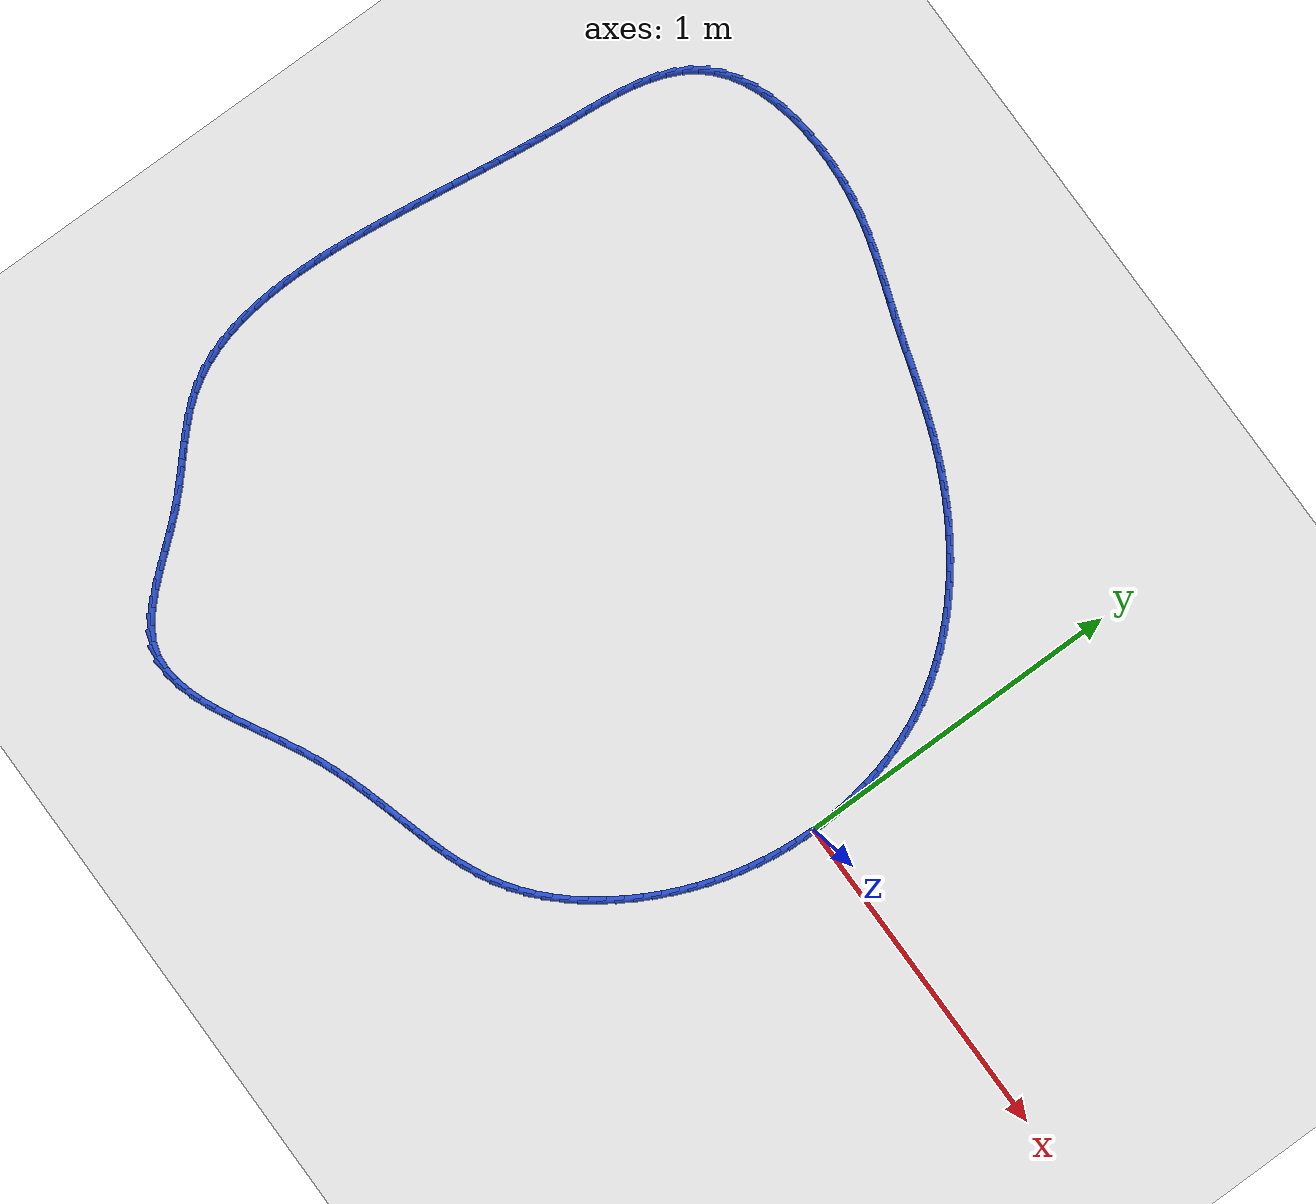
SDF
<sdf version="1.6">
 <world name="default">
  <light name="sun" type="directional">
   <pose>0 0 10 0 -0 0</pose>
   <diffuse>0.8 0.8 0.8 1</diffuse>
   <specular>0.2 0.2 0.2 1</specular>
   <attenuation>
    <range>1000</range>
    <constant>0.9</constant>
    <linear>0.01</linear>
    <quadratic>0.001</quadratic>
   </attenuation>
   <direction>-0.5 0.1 -0.9</direction>
  </light>
  <model name="ground_plane">
   <static>1</static>
   <link name="link">
    <collision name="collision">
     <geometry><plane><normal>0 0 1</normal><size>100 100</size></plane></geometry>
     <surface><friction><ode><mu>100</mu><mu2>50</mu2></ode></friction></surface>
    </collision>
    <visual name="visual">
     <cast_shadows>0</cast_shadows>
     <geometry><plane><normal>0 0 1</normal><size>100 100</size></plane></geometry>
     <material>
      <script><uri>file://media/materials/scripts/gazebo.material</uri><name>Gazebo/WhiteGlow</name></script>
     </material>
    </visual>
   </link>
  </model>
  <gravity>0 0 -9.8</gravity>
  <magnetic_field>6e-06 2.3e-05 -4.2e-05</magnetic_field>
  <atmosphere type="adiabatic"/>
  <physics name="default_physics" default="0" type="ode">
   <max_step_size>0.001</max_step_size>
   <real_time_factor>1</real_time_factor>
   <real_time_update_rate>1000</real_time_update_rate>
  </physics>
  <scene><ambient>0.4 0.4 0.4 1</ambient><background>0.7 0.7 0.7 1</background><shadows>1</shadows></scene>
  <spherical_coordinates>
   <surface_model>EARTH_WGS84</surface_model>
   <latitude_deg>0</latitude_deg>
   <longitude_deg>0</longitude_deg>
   <elevation>0</elevation>
   <heading_deg>0</heading_deg>
  </spherical_coordinates>
  <model name="line">
   <link name="link_0">
    <pose>6.938893903907228e-18 6.938893903907228e-17 0.01 0 1.57 -1.5540113074684683</pose>
    <collision name="collision">
     <geometry><cylinder><radius>0.01</radius><length>0.08</length></cylinder></geometry>
    </collision>
    <visual name="visual">
     <material>
      <script><name>Gazebo/Blue</name><uri>file://media/materials/scripts/gazebo.material</uri></script>
     </material>
     <geometry><cylinder><radius>0.01</radius><length>0.08</length></cylinder></geometry>
    </visual>
   </link>
   <link name="link_1">
    <pose>-0.000846863289266111 0.05044878057227724 0.01 0 1.57 -1.5048120460281225</pose>
    <collision name="collision">
     <geometry><cylinder><radius>0.01</radius><length>0.08</length></cylinder></geometry>
    </collision>
    <visual name="visual">
     <material>
      <script><name>Gazebo/Blue</name><uri>file://media/materials/scripts/gazebo.material</uri></script>
     </material>
     <geometry><cylinder><radius>0.01</radius><length>0.08</length></cylinder></geometry>
    </visual>
   </link>
   <link name="link_2">
    <pose>-0.004183027712462349 0.10093536881632155 0.01 0 1.57 -1.4546045815174098</pose>
    <collision name="collision">
     <geometry><cylinder><radius>0.01</radius><length>0.08</length></cylinder></geometry>
    </collision>
    <visual name="visual">
     <material>
      <script><name>Gazebo/Blue</name><uri>file://media/materials/scripts/gazebo.material</uri></script>
     </material>
     <geometry><cylinder><radius>0.01</radius><length>0.08</length></cylinder></geometry>
    </visual>
   </link>
   <link name="link_3">
    <pose>-0.010055983220984638 0.1512530773212387 0.01 0 1.57 -1.4030470330745322</pose>
    <collision name="collision">
     <geometry><cylinder><radius>0.01</radius><length>0.08</length></cylinder></geometry>
    </collision>
    <visual name="visual">
     <material>
      <script><name>Gazebo/Blue</name><uri>file://media/materials/scripts/gazebo.material</uri></script>
     </material>
     <geometry><cylinder><radius>0.01</radius><length>0.08</length></cylinder></geometry>
    </visual>
   </link>
   <link name="link_4">
    <pose>-0.018513219766228918 0.20119521867613424 0.01 0 1.57 -1.3498090857388654</pose>
    <collision name="collision">
     <geometry><cylinder><radius>0.01</radius><length>0.08</length></cylinder></geometry>
    </collision>
    <visual name="visual">
     <material>
      <script><name>Gazebo/Blue</name><uri>file://media/materials/scripts/gazebo.material</uri></script>
     </material>
     <geometry><cylinder><radius>0.01</radius><length>0.08</length></cylinder></geometry>
    </visual>
   </link>
   <link name="link_5">
    <pose>-0.029602227299591173 0.25055510547011406 0.01 0 1.57 -1.2945754169645705</pose>
    <collision name="collision">
     <geometry><cylinder><radius>0.01</radius><length>0.08</length></cylinder></geometry>
    </collision>
    <visual name="visual">
     <material>
      <script><name>Gazebo/Blue</name><uri>file://media/materials/scripts/gazebo.material</uri></script>
     </material>
     <geometry><cylinder><radius>0.01</radius><length>0.08</length></cylinder></geometry>
    </visual>
   </link>
   <link name="link_6">
    <pose>-0.043370495772467335 0.2991260502922837 0.01 0 1.57 -1.2370520561739902</pose>
    <collision name="collision">
     <geometry><cylinder><radius>0.01</radius><length>0.08</length></cylinder></geometry>
    </collision>
    <visual name="visual">
     <material>
      <script><name>Gazebo/Blue</name><uri>file://media/materials/scripts/gazebo.material</uri></script>
     </material>
     <geometry><cylinder><radius>0.01</radius><length>0.08</length></cylinder></geometry>
    </visual>
   </link>
   <link name="link_7">
    <pose>-0.059865515136253294 0.3467013657317487 0.01 0 1.57 -1.1769761766404556</pose>
    <collision name="collision">
     <geometry><cylinder><radius>0.01</radius><length>0.08</length></cylinder></geometry>
    </collision>
    <visual name="visual">
     <material>
      <script><name>Gazebo/Blue</name><uri>file://media/materials/scripts/gazebo.material</uri></script>
     </material>
     <geometry><cylinder><radius>0.01</radius><length>0.08</length></cylinder></geometry>
    </visual>
   </link>
   <link name="link_8">
    <pose>-0.07913477534234509 0.3930743643776149 0.01 0 1.57 -1.1141304534891028</pose>
    <collision name="collision">
     <geometry><cylinder><radius>0.01</radius><length>0.08</length></cylinder></geometry>
    </collision>
    <visual name="visual">
     <material>
      <script><name>Gazebo/Blue</name><uri>file://media/materials/scripts/gazebo.material</uri></script>
     </material>
     <geometry><cylinder><radius>0.01</radius><length>0.08</length></cylinder></geometry>
    </visual>
   </link>
   <link name="link_9">
    <pose>-0.1012257362384151 0.4380383859566431 0.01 0 1.57 -1.0496096226033214</pose>
    <collision name="collision">
     <geometry><cylinder><radius>0.01</radius><length>0.08</length></cylinder></geometry>
    </collision>
    <visual name="visual">
     <material>
      <script><name>Gazebo/Blue</name><uri>file://media/materials/scripts/gazebo.material</uri></script>
     </material>
     <geometry><cylinder><radius>0.01</radius><length>0.08</length></cylinder></geometry>
    </visual>
   </link>
   <link name="link_10">
    <pose>-0.12613832176934947 0.4814296224669828 0.01 0 1.57 -0.9872117548518307</pose>
    <collision name="collision">
     <geometry><cylinder><radius>0.01</radius><length>0.08</length></cylinder></geometry>
    </collision>
    <visual name="visual">
     <material>
      <script><name>Gazebo/Blue</name><uri>file://media/materials/scripts/gazebo.material</uri></script>
     </material>
     <geometry><cylinder><radius>0.01</radius><length>0.08</length></cylinder></geometry>
    </visual>
   </link>
   <link name="link_11">
    <pose>-0.15372864336731643 0.5232139088179921 0.01 0 1.57 -0.92775134159099</pose>
    <collision name="collision">
     <geometry><cylinder><radius>0.01</radius><length>0.08</length></cylinder></geometry>
    </collision>
    <visual name="visual">
     <material>
      <script><name>Gazebo/Blue</name><uri>file://media/materials/scripts/gazebo.material</uri></script>
     </material>
     <geometry><cylinder><radius>0.01</radius><length>0.08</length></cylinder></geometry>
    </visual>
   </link>
   <link name="link_12">
    <pose>-0.18382572097345248 0.5633815021316724 0.01 0 1.57 -0.8712505623732291</pose>
    <collision name="collision">
     <geometry><cylinder><radius>0.01</radius><length>0.08</length></cylinder></geometry>
    </collision>
    <visual name="visual">
     <material>
      <script><name>Gazebo/Blue</name><uri>file://media/materials/scripts/gazebo.material</uri></script>
     </material>
     <geometry><cylinder><radius>0.01</radius><length>0.08</length></cylinder></geometry>
    </visual>
   </link>
   <link name="link_13">
    <pose>-0.21625857452889397 0.6019226595300242 0.01 0 1.57 -0.8176561215939029</pose>
    <collision name="collision">
     <geometry><cylinder><radius>0.01</radius><length>0.08</length></cylinder></geometry>
    </collision>
    <visual name="visual">
     <material>
      <script><name>Gazebo/Blue</name><uri>file://media/materials/scripts/gazebo.material</uri></script>
     </material>
     <geometry><cylinder><radius>0.01</radius><length>0.08</length></cylinder></geometry>
    </visual>
   </link>
   <link name="link_14">
    <pose>-0.25085622397477736 0.6388276381350487 0.01 0 1.57 -0.7668561180237977</pose>
    <collision name="collision">
     <geometry><cylinder><radius>0.01</radius><length>0.08</length></cylinder></geometry>
    </collision>
    <visual name="visual">
     <material>
      <script><name>Gazebo/Blue</name><uri>file://media/materials/scripts/gazebo.material</uri></script>
     </material>
     <geometry><cylinder><radius>0.01</radius><length>0.08</length></cylinder></geometry>
    </visual>
   </link>
   <link name="link_15">
    <pose>-0.2874476892522393 0.6740866950687473 0.01 0 1.57 -0.7186955053466644</pose>
    <collision name="collision">
     <geometry><cylinder><radius>0.01</radius><length>0.08</length></cylinder></geometry>
    </collision>
    <visual name="visual">
     <material>
      <script><name>Gazebo/Blue</name><uri>file://media/materials/scripts/gazebo.material</uri></script>
     </material>
     <geometry><cylinder><radius>0.01</radius><length>0.08</length></cylinder></geometry>
    </visual>
   </link>
   <link name="link_16">
    <pose>-0.32586199030241625 0.7076900874531212 0.01 0 1.57 -0.6729892447350059</pose>
    <collision name="collision">
     <geometry><cylinder><radius>0.01</radius><length>0.08</length></cylinder></geometry>
    </collision>
    <visual name="visual">
     <material>
      <script><name>Gazebo/Blue</name><uri>file://media/materials/scripts/gazebo.material</uri></script>
     </material>
     <geometry><cylinder><radius>0.01</radius><length>0.08</length></cylinder></geometry>
    </visual>
   </link>
   <link name="link_17">
    <pose>-0.3659281470664446 0.739628072410171 0.01 0 1.57 -0.629532814763707</pose>
    <collision name="collision">
     <geometry><cylinder><radius>0.01</radius><length>0.08</length></cylinder></geometry>
    </collision>
    <visual name="visual">
     <material>
      <script><name>Gazebo/Blue</name><uri>file://media/materials/scripts/gazebo.material</uri></script>
     </material>
     <geometry><cylinder><radius>0.01</radius><length>0.08</length></cylinder></geometry>
    </visual>
   </link>
   <link name="link_18">
    <pose>-0.40747517948546075 0.769890907061898 0.01 0 1.57 -0.5881101183981946</pose>
    <collision name="collision">
     <geometry><cylinder><radius>0.01</radius><length>0.08</length></cylinder></geometry>
    </collision>
    <visual name="visual">
     <material>
      <script><name>Gazebo/Blue</name><uri>file://media/materials/scripts/gazebo.material</uri></script>
     </material>
     <geometry><cylinder><radius>0.01</radius><length>0.08</length></cylinder></geometry>
    </visual>
   </link>
   <link name="link_19">
    <pose>-0.4503321075006014 0.7984688485303034 0.01 0 1.57 -0.5484990349841696</pose>
    <collision name="collision">
     <geometry><cylinder><radius>0.01</radius><length>0.08</length></cylinder></geometry>
    </collision>
    <visual name="visual">
     <material>
      <script><name>Gazebo/Blue</name><uri>file://media/materials/scripts/gazebo.material</uri></script>
     </material>
     <geometry><cylinder><radius>0.01</radius><length>0.08</length></cylinder></geometry>
    </visual>
   </link>
   <link name="link_20">
    <pose>-0.494327951053003 0.825352153937388 0.01 0 1.57 -0.5104749501543075</pose>
    <collision name="collision">
     <geometry><cylinder><radius>0.01</radius><length>0.08</length></cylinder></geometry>
    </collision>
    <visual name="visual">
     <material>
      <script><name>Gazebo/Blue</name><uri>file://media/materials/scripts/gazebo.material</uri></script>
     </material>
     <geometry><cylinder><radius>0.01</radius><length>0.08</length></cylinder></geometry>
    </visual>
   </link>
   <link name="link_21">
    <pose>-0.5392917300838019 0.8505310804051531 0.01 0 1.57 -0.4738126013549564</pose>
    <collision name="collision">
     <geometry><cylinder><radius>0.01</radius><length>0.08</length></cylinder></geometry>
    </collision>
    <visual name="visual">
     <material>
      <script><name>Gazebo/Blue</name><uri>file://media/materials/scripts/gazebo.material</uri></script>
     </material>
     <geometry><cylinder><radius>0.01</radius><length>0.08</length></cylinder></geometry>
    </visual>
   </link>
   <link name="link_22">
    <pose>-0.5850524645341345 0.8739958850555999 0.01 0 1.57 -0.43828653546666146</pose>
    <collision name="collision">
     <geometry><cylinder><radius>0.01</radius><length>0.08</length></cylinder></geometry>
    </collision>
    <visual name="visual">
     <material>
      <script><name>Gazebo/Blue</name><uri>file://media/materials/scripts/gazebo.material</uri></script>
     </material>
     <geometry><cylinder><radius>0.01</radius><length>0.08</length></cylinder></geometry>
    </visual>
   </link>
   <link name="link_23">
    <pose>-0.6314391743451375 0.8957368250107292 0.01 0 1.57 -0.40379949012489236</pose>
    <collision name="collision">
     <geometry><cylinder><radius>0.01</radius><length>0.08</length></cylinder></geometry>
    </collision>
    <visual name="visual">
     <material>
      <script><name>Gazebo/Blue</name><uri>file://media/materials/scripts/gazebo.material</uri></script>
     </material>
     <geometry><cylinder><radius>0.01</radius><length>0.08</length></cylinder></geometry>
    </visual>
   </link>
   <link name="link_24">
    <pose>-0.6782826554844723 0.9157520659899898 0.01 0 1.57 -0.3727277492750169</pose>
    <collision name="collision">
     <geometry><cylinder><radius>0.01</radius><length>0.08</length></cylinder></geometry>
    </collision>
    <visual name="visual">
     <material>
      <script><name>Gazebo/Blue</name><uri>file://media/materials/scripts/gazebo.material</uri></script>
     </material>
     <geometry><cylinder><radius>0.01</radius><length>0.08</length></cylinder></geometry>
    </visual>
   </link>
   <link name="link_25">
    <pose>-0.7254483543583417 0.9341940711661418 0.01 0 1.57 -0.3474792417741428</pose>
    <collision name="collision">
     <geometry><cylinder><radius>0.01</radius><length>0.08</length></cylinder></geometry>
    </collision>
    <visual name="visual">
     <material>
      <script><name>Gazebo/Blue</name><uri>file://media/materials/scripts/gazebo.material</uri></script>
     </material>
     <geometry><cylinder><radius>0.01</radius><length>0.08</length></cylinder></geometry>
    </visual>
   </link>
   <link name="link_26">
    <pose>-0.7728332385817407 0.9513556667909308 0.01 0 1.57 -0.3282740059276123</pose>
    <collision name="collision">
     <geometry><cylinder><radius>0.01</radius><length>0.08</length></cylinder></geometry>
    </collision>
    <visual name="visual">
     <material>
      <script><name>Gazebo/Blue</name><uri>file://media/materials/scripts/gazebo.material</uri></script>
     </material>
     <geometry><cylinder><radius>0.01</radius><length>0.08</length></cylinder></geometry>
    </visual>
   </link>
   <link name="link_27">
    <pose>-0.8203354241921299 0.9675347930098726 0.01 0 1.57 -0.3152094953519339</pose>
    <collision name="collision">
     <geometry><cylinder><radius>0.01</radius><length>0.08</length></cylinder></geometry>
    </collision>
    <visual name="visual">
     <material>
      <script><name>Gazebo/Blue</name><uri>file://media/materials/scripts/gazebo.material</uri></script>
     </material>
     <geometry><cylinder><radius>0.01</radius><length>0.08</length></cylinder></geometry>
    </visual>
   </link>
   <link name="link_28">
    <pose>-0.8678530272269706 0.9830293899684845 0.01 0 1.57 -0.3083644798377469</pose>
    <collision name="collision">
     <geometry><cylinder><radius>0.01</radius><length>0.08</length></cylinder></geometry>
    </collision>
    <visual name="visual">
     <material>
      <script><name>Gazebo/Blue</name><uri>file://media/materials/scripts/gazebo.material</uri></script>
     </material>
     <geometry><cylinder><radius>0.01</radius><length>0.08</length></cylinder></geometry>
    </visual>
   </link>
   <link name="link_29">
    <pose>-0.9152841637237231 0.9981373978122828 0.01 0 1.57 -0.3078137139429258</pose>
    <collision name="collision">
     <geometry><cylinder><radius>0.01</radius><length>0.08</length></cylinder></geometry>
    </collision>
    <visual name="visual">
     <material>
      <script><name>Gazebo/Blue</name><uri>file://media/materials/scripts/gazebo.material</uri></script>
     </material>
     <geometry><cylinder><radius>0.01</radius><length>0.08</length></cylinder></geometry>
    </visual>
   </link>
   <link name="link_30">
    <pose>-0.9625269497198491 1.013156756686784 0.01 0 1.57 -0.313635982248948</pose>
    <collision name="collision">
     <geometry><cylinder><radius>0.01</radius><length>0.08</length></cylinder></geometry>
    </collision>
    <visual name="visual">
     <material>
      <script><name>Gazebo/Blue</name><uri>file://media/materials/scripts/gazebo.material</uri></script>
     </material>
     <geometry><cylinder><radius>0.01</radius><length>0.08</length></cylinder></geometry>
    </visual>
   </link>
   <link name="link_31">
    <pose>-1.009479501252808 1.0283854067375042 0.01 0 1.57 -0.32569144161398295</pose>
    <collision name="collision">
     <geometry><cylinder><radius>0.01</radius><length>0.08</length></cylinder></geometry>
    </collision>
    <visual name="visual">
     <material>
      <script><name>Gazebo/Blue</name><uri>file://media/materials/scripts/gazebo.material</uri></script>
     </material>
     <geometry><cylinder><radius>0.01</radius><length>0.08</length></cylinder></geometry>
    </visual>
   </link>
   <link name="link_32">
    <pose>-1.0560456580611934 1.0441116304607445 0.01 0 1.57 -0.33610510327911913</pose>
    <collision name="collision">
     <geometry><cylinder><radius>0.01</radius><length>0.08</length></cylinder></geometry>
    </collision>
    <visual name="visual">
     <material>
      <script><name>Gazebo/Blue</name><uri>file://media/materials/scripts/gazebo.material</uri></script>
     </material>
     <geometry><cylinder><radius>0.01</radius><length>0.08</length></cylinder></geometry>
    </visual>
   </link>
   <link name="link_33">
    <pose>-1.1023316904823954 1.0602821474953277 0.01 0 1.57 -0.33492636460139485</pose>
    <collision name="collision">
     <geometry><cylinder><radius>0.01</radius><length>0.08</length></cylinder></geometry>
    </collision>
    <visual name="visual">
     <material>
      <script><name>Gazebo/Blue</name><uri>file://media/materials/scripts/gazebo.material</uri></script>
     </material>
     <geometry><cylinder><radius>0.01</radius><length>0.08</length></cylinder></geometry>
    </visual>
   </link>
   <link name="link_34">
    <pose>-1.1486957737757293 1.076418636179721 0.01 0 1.57 -0.3216001345120442</pose>
    <collision name="collision">
     <geometry><cylinder><radius>0.01</radius><length>0.08</length></cylinder></geometry>
    </collision>
    <visual name="visual">
     <material>
      <script><name>Gazebo/Blue</name><uri>file://media/materials/scripts/gazebo.material</uri></script>
     </material>
     <geometry><cylinder><radius>0.01</radius><length>0.08</length></cylinder></geometry>
    </visual>
   </link>
   <link name="link_35">
    <pose>-1.1955118502999573 1.0920161708924527 0.01 0 1.57 -0.2964761904887157</pose>
    <collision name="collision">
     <geometry><cylinder><radius>0.01</radius><length>0.08</length></cylinder></geometry>
    </collision>
    <visual name="visual">
     <material>
      <script><name>Gazebo/Blue</name><uri>file://media/materials/scripts/gazebo.material</uri></script>
     </material>
     <geometry><cylinder><radius>0.01</radius><length>0.08</length></cylinder></geometry>
    </visual>
   </link>
   <link name="link_36">
    <pose>-1.2431538624138403 1.1065698260120493 0.01 0 1.57 -0.26022666689466184</pose>
    <collision name="collision">
     <geometry><cylinder><radius>0.01</radius><length>0.08</length></cylinder></geometry>
    </collision>
    <visual name="visual">
     <material>
      <script><name>Gazebo/Blue</name><uri>file://media/materials/scripts/gazebo.material</uri></script>
     </material>
     <geometry><cylinder><radius>0.01</radius><length>0.08</length></cylinder></geometry>
    </visual>
   </link>
   <link name="link_37">
    <pose>-1.2919957524761405 1.119574675917039 0.01 0 1.57 -0.21389366517273364</pose>
    <collision name="collision">
     <geometry><cylinder><radius>0.01</radius><length>0.08</length></cylinder></geometry>
    </collision>
    <visual name="visual">
     <material>
      <script><name>Gazebo/Blue</name><uri>file://media/materials/scripts/gazebo.material</uri></script>
     </material>
     <geometry><cylinder><radius>0.01</radius><length>0.08</length></cylinder></geometry>
    </visual>
   </link>
   <link name="link_38">
    <pose>-1.342411462845619 1.1305257949859497 0.01 0 1.57 -0.1591375782966789</pose>
    <collision name="collision">
     <geometry><cylinder><radius>0.01</radius><length>0.08</length></cylinder></geometry>
    </collision>
    <visual name="visual">
     <material>
      <script><name>Gazebo/Blue</name><uri>file://media/materials/scripts/gazebo.material</uri></script>
     </material>
     <geometry><cylinder><radius>0.01</radius><length>0.08</length></cylinder></geometry>
    </visual>
   </link>
   <link name="link_39">
    <pose>-1.3947478460285339 1.1389255071886293 0.01 0 1.57 -0.10139241929132188</pose>
    <collision name="collision">
     <geometry><cylinder><radius>0.01</radius><length>0.08</length></cylinder></geometry>
    </collision>
    <visual name="visual">
     <material>
      <script><name>Gazebo/Blue</name><uri>file://media/materials/scripts/gazebo.material</uri></script>
     </material>
     <geometry><cylinder><radius>0.01</radius><length>0.08</length></cylinder></geometry>
    </visual>
   </link>
   <link name="link_40">
    <pose>-1.4487971548328704 1.144424554473884 0.01 0 1.57 -0.04336346354686689</pose>
    <collision name="collision">
     <geometry><cylinder><radius>0.01</radius><length>0.08</length></cylinder></geometry>
    </collision>
    <visual name="visual">
     <material>
      <script><name>Gazebo/Blue</name><uri>file://media/materials/scripts/gazebo.material</uri></script>
     </material>
     <geometry><cylinder><radius>0.01</radius><length>0.08</length></cylinder></geometry>
    </visual>
   </link>
   <link name="link_41">
    <pose>-1.5038326067665755 1.1468125792812347 0.01 0 1.57 0.016787465859608688</pose>
    <collision name="collision">
     <geometry><cylinder><radius>0.01</radius><length>0.08</length></cylinder></geometry>
    </collision>
    <visual name="visual">
     <material>
      <script><name>Gazebo/Blue</name><uri>file://media/materials/scripts/gazebo.material</uri></script>
     </material>
     <geometry><cylinder><radius>0.01</radius><length>0.08</length></cylinder></geometry>
    </visual>
   </link>
   <link name="link_42">
    <pose>-1.5591074521599775 1.1458845675225415 0.01 0 1.57 0.08105747216658196</pose>
    <collision name="collision">
     <geometry><cylinder><radius>0.01</radius><length>0.08</length></cylinder></geometry>
    </collision>
    <visual name="visual">
     <material>
      <script><name>Gazebo/Blue</name><uri>file://media/materials/scripts/gazebo.material</uri></script>
     </material>
     <geometry><cylinder><radius>0.01</radius><length>0.08</length></cylinder></geometry>
    </visual>
   </link>
   <link name="link_43">
    <pose>-1.6138749413434055 1.1414355051096652 0.01 0 1.57 0.15159583432409895</pose>
    <collision name="collision">
     <geometry><cylinder><radius>0.01</radius><length>0.08</length></cylinder></geometry>
    </collision>
    <visual name="visual">
     <material>
      <script><name>Gazebo/Blue</name><uri>file://media/materials/scripts/gazebo.material</uri></script>
     </material>
     <geometry><cylinder><radius>0.01</radius><length>0.08</length></cylinder></geometry>
    </visual>
   </link>
   <link name="link_44">
    <pose>-1.6673883246471901 1.1332603779544663 0.01 0 1.57 0.23082597803693913</pose>
    <collision name="collision">
     <geometry><cylinder><radius>0.01</radius><length>0.08</length></cylinder></geometry>
    </collision>
    <visual name="visual">
     <material>
      <script><name>Gazebo/Blue</name><uri>file://media/materials/scripts/gazebo.material</uri></script>
     </material>
     <geometry><cylinder><radius>0.01</radius><length>0.08</length></cylinder></geometry>
    </visual>
   </link>
   <link name="link_45">
    <pose>-1.718900852401659 1.1211541719688052 0.01 0 1.57 0.32151660270292787</pose>
    <collision name="collision">
     <geometry><cylinder><radius>0.01</radius><length>0.08</length></cylinder></geometry>
    </collision>
    <visual name="visual">
     <material>
      <script><name>Gazebo/Blue</name><uri>file://media/materials/scripts/gazebo.material</uri></script>
     </material>
     <geometry><cylinder><radius>0.01</radius><length>0.08</length></cylinder></geometry>
    </visual>
   </link>
   <link name="link_46">
    <pose>-1.7676657749371425 1.1049118730645424 0.01 0 1.57 0.4267350443168989</pose>
    <collision name="collision">
     <geometry><cylinder><radius>0.01</radius><length>0.08</length></cylinder></geometry>
    </collision>
    <visual name="visual">
     <material>
      <script><name>Gazebo/Blue</name><uri>file://media/materials/scripts/gazebo.material</uri></script>
     </material>
     <geometry><cylinder><radius>0.01</radius><length>0.08</length></cylinder></geometry>
    </visual>
   </link>
   <link name="link_47">
    <pose>-1.8129363425839689 1.0843284671535387 0.01 0 1.57 0.549541950563444</pose>
    <collision name="collision">
     <geometry><cylinder><radius>0.01</radius><length>0.08</length></cylinder></geometry>
    </collision>
    <visual name="visual">
     <material>
      <script><name>Gazebo/Blue</name><uri>file://media/materials/scripts/gazebo.material</uri></script>
     </material>
     <geometry><cylinder><radius>0.01</radius><length>0.08</length></cylinder></geometry>
    </visual>
   </link>
   <link name="link_48">
    <pose>-1.8539658056724684 1.0591989401476543 0.01 0 1.57 0.6922111007255526</pose>
    <collision name="collision">
     <geometry><cylinder><radius>0.01</radius><length>0.08</length></cylinder></geometry>
    </collision>
    <visual name="visual">
     <material>
      <script><name>Gazebo/Blue</name><uri>file://media/materials/scripts/gazebo.material</uri></script>
     </material>
     <geometry><cylinder><radius>0.01</radius><length>0.08</length></cylinder></geometry>
    </visual>
   </link>
   <link name="link_49">
    <pose>-1.8900074145329693 1.0293182779587495 0.01 0 1.57 0.8545032119874683</pose>
    <collision name="collision">
     <geometry><cylinder><radius>0.01</radius><length>0.08</length></cylinder></geometry>
    </collision>
    <visual name="visual">
     <material>
      <script><name>Gazebo/Blue</name><uri>file://media/materials/scripts/gazebo.material</uri></script>
     </material>
     <geometry><cylinder><radius>0.01</radius><length>0.08</length></cylinder></geometry>
    </visual>
   </link>
   <link name="link_50">
    <pose>-1.9203271336976069 0.9944892726972168 0.01 0 1.57 1.017493949531124</pose>
    <collision name="collision">
     <geometry><cylinder><radius>0.01</radius><length>0.08</length></cylinder></geometry>
    </collision>
    <visual name="visual">
     <material>
      <script><name>Gazebo/Blue</name><uri>file://media/materials/scripts/gazebo.material</uri></script>
     </material>
     <geometry><cylinder><radius>0.01</radius><length>0.08</length></cylinder></geometry>
    </visual>
   </link>
   <link name="link_51">
    <pose>-1.9447904069987882 0.9548827816107704 0.01 0 1.57 1.1545128135580256</pose>
    <collision name="collision">
     <geometry><cylinder><radius>0.01</radius><length>0.08</length></cylinder></geometry>
    </collision>
    <visual name="visual">
     <material>
      <script><name>Gazebo/Blue</name><uri>file://media/materials/scripts/gazebo.material</uri></script>
     </material>
     <geometry><cylinder><radius>0.01</radius><length>0.08</length></cylinder></geometry>
    </visual>
   </link>
   <link name="link_52">
    <pose>-1.9641084302780705 0.9111889323026608 0.01 0 1.57 1.2631930272044491</pose>
    <collision name="collision">
     <geometry><cylinder><radius>0.01</radius><length>0.08</length></cylinder></geometry>
    </collision>
    <visual name="visual">
     <material>
      <script><name>Gazebo/Blue</name><uri>file://media/materials/scripts/gazebo.material</uri></script>
     </material>
     <geometry><cylinder><radius>0.01</radius><length>0.08</length></cylinder></geometry>
    </visual>
   </link>
   <link name="link_53">
    <pose>-1.9790562043151552 0.8641370269953603 0.01 0 1.57 1.346143572806285</pose>
    <collision name="collision">
     <geometry><cylinder><radius>0.01</radius><length>0.08</length></cylinder></geometry>
    </collision>
    <visual name="visual">
     <material>
      <script><name>Gazebo/Blue</name><uri>file://media/materials/scripts/gazebo.material</uri></script>
     </material>
     <geometry><cylinder><radius>0.01</radius><length>0.08</length></cylinder></geometry>
    </visual>
   </link>
   <link name="link_54">
    <pose>-1.9904087298897393 0.8144563679113388 0.01 0 1.57 1.4068628297916659</pose>
    <collision name="collision">
     <geometry><cylinder><radius>0.01</radius><length>0.08</length></cylinder></geometry>
    </collision>
    <visual name="visual">
     <material>
      <script><name>Gazebo/Blue</name><uri>file://media/materials/scripts/gazebo.material</uri></script>
     </material>
     <geometry><cylinder><radius>0.01</radius><length>0.08</length></cylinder></geometry>
    </visual>
   </link>
   <link name="link_55">
    <pose>-1.9989410077815235 0.7628762572730675 0.01 0 1.57 1.4484344072373352</pose>
    <collision name="collision">
     <geometry><cylinder><radius>0.01</radius><length>0.08</length></cylinder></geometry>
    </collision>
    <visual name="visual">
     <material>
      <script><name>Gazebo/Blue</name><uri>file://media/materials/scripts/gazebo.material</uri></script>
     </material>
     <geometry><cylinder><radius>0.01</radius><length>0.08</length></cylinder></geometry>
    </visual>
   </link>
   <link name="link_56">
    <pose>-2.005428038770206 0.7101259973030183 0.01 0 1.57 1.4730327275939075</pose>
    <collision name="collision">
     <geometry><cylinder><radius>0.01</radius><length>0.08</length></cylinder></geometry>
    </collision>
    <visual name="visual">
     <material>
      <script><name>Gazebo/Blue</name><uri>file://media/materials/scripts/gazebo.material</uri></script>
     </material>
     <geometry><cylinder><radius>0.01</radius><length>0.08</length></cylinder></geometry>
    </visual>
   </link>
   <link name="link_57">
    <pose>-2.010644823635487 0.6569348902236612 0.01 0 1.57 1.481782591790295</pose>
    <collision name="collision">
     <geometry><cylinder><radius>0.01</radius><length>0.08</length></cylinder></geometry>
    </collision>
    <visual name="visual">
     <material>
      <script><name>Gazebo/Blue</name><uri>file://media/materials/scripts/gazebo.material</uri></script>
     </material>
     <geometry><cylinder><radius>0.01</radius><length>0.08</length></cylinder></geometry>
    </visual>
   </link>
   <link name="link_58">
    <pose>-2.015366363157065 0.6040322382574687 0.01 0 1.57 1.4753517745678855</pose>
    <collision name="collision">
     <geometry><cylinder><radius>0.01</radius><length>0.08</length></cylinder></geometry>
    </collision>
    <visual name="visual">
     <material>
      <script><name>Gazebo/Blue</name><uri>file://media/materials/scripts/gazebo.material</uri></script>
     </material>
     <geometry><cylinder><radius>0.01</radius><length>0.08</length></cylinder></geometry>
    </visual>
   </link>
   <link name="link_59">
    <pose>-2.0203369404370792 0.5521123060791184 0.01 0 1.57 1.462765319706587</pose>
    <collision name="collision">
     <geometry><cylinder><radius>0.01</radius><length>0.08</length></cylinder></geometry>
    </collision>
    <visual name="visual">
     <material>
      <script><name>Gazebo/Blue</name><uri>file://media/materials/scripts/gazebo.material</uri></script>
     </material>
     <geometry><cylinder><radius>0.01</radius><length>0.08</length></cylinder></geometry>
    </visual>
   </link>
   <link name="link_60">
    <pose>-2.025842633454997 0.5013467152092551 0.01 0 1.57 1.4514870694990758</pose>
    <collision name="collision">
     <geometry><cylinder><radius>0.01</radius><length>0.08</length></cylinder></geometry>
    </collision>
    <visual name="visual">
     <material>
      <script><name>Gazebo/Blue</name><uri>file://media/materials/scripts/gazebo.material</uri></script>
     </material>
     <geometry><cylinder><radius>0.01</radius><length>0.08</length></cylinder></geometry>
    </visual>
   </link>
   <link name="link_61">
    <pose>-2.031817519024674 0.4515055835835264 0.01 0 1.57 1.4419463805792232</pose>
    <collision name="collision">
     <geometry><cylinder><radius>0.01</radius><length>0.08</length></cylinder></geometry>
    </collision>
    <visual name="visual">
     <material>
      <script><name>Gazebo/Blue</name><uri>file://media/materials/scripts/gazebo.material</uri></script>
     </material>
     <geometry><cylinder><radius>0.01</radius><length>0.08</length></cylinder></geometry>
    </visual>
   </link>
   <link name="link_62">
    <pose>-2.038186661105561 0.40234874879277044 0.01 0 1.57 1.434345251638677</pose>
    <collision name="collision">
     <geometry><cylinder><radius>0.01</radius><length>0.08</length></cylinder></geometry>
    </collision>
    <visual name="visual">
     <material>
      <script><name>Gazebo/Blue</name><uri>file://media/materials/scripts/gazebo.material</uri></script>
     </material>
     <geometry><cylinder><radius>0.01</radius><length>0.08</length></cylinder></geometry>
    </visual>
   </link>
   <link name="link_63">
    <pose>-2.0448751236571066 0.35363604842782387 0.01 0 1.57 1.428838086350353</pose>
    <collision name="collision">
     <geometry><cylinder><radius>0.01</radius><length>0.08</length></cylinder></geometry>
    </collision>
    <visual name="visual">
     <material>
      <script><name>Gazebo/Blue</name><uri>file://media/materials/scripts/gazebo.material</uri></script>
     </material>
     <geometry><cylinder><radius>0.01</radius><length>0.08</length></cylinder></geometry>
    </visual>
   </link>
   <link name="link_64">
    <pose>-2.0518079706387584 0.3051273200795243 0.01 0 1.57 1.4255234061139481</pose>
    <collision name="collision">
     <geometry><cylinder><radius>0.01</radius><length>0.08</length></cylinder></geometry>
    </collision>
    <visual name="visual">
     <material>
      <script><name>Gazebo/Blue</name><uri>file://media/materials/scripts/gazebo.material</uri></script>
     </material>
     <geometry><cylinder><radius>0.01</radius><length>0.08</length></cylinder></geometry>
    </visual>
   </link>
   <link name="link_65">
    <pose>-2.058910266009967 0.25658240133870885 0.01 0 1.57 1.4244390592110066</pose>
    <collision name="collision">
     <geometry><cylinder><radius>0.01</radius><length>0.08</length></cylinder></geometry>
    </collision>
    <visual name="visual">
     <material>
      <script><name>Gazebo/Blue</name><uri>file://media/materials/scripts/gazebo.material</uri></script>
     </material>
     <geometry><cylinder><radius>0.01</radius><length>0.08</length></cylinder></geometry>
    </visual>
   </link>
   <link name="link_66">
    <pose>-2.06610707373018 0.20776112979621408 0.01 0 1.57 1.425561323069314</pose>
    <collision name="collision">
     <geometry><cylinder><radius>0.01</radius><length>0.08</length></cylinder></geometry>
    </collision>
    <visual name="visual">
     <material>
      <script><name>Gazebo/Blue</name><uri>file://media/materials/scripts/gazebo.material</uri></script>
     </material>
     <geometry><cylinder><radius>0.01</radius><length>0.08</length></cylinder></geometry>
    </visual>
   </link>
   <link name="link_67">
    <pose>-2.073323457758846 0.15842334304287814 0.01 0 1.57 1.4288078701041589</pose>
    <collision name="collision">
     <geometry><cylinder><radius>0.01</radius><length>0.08</length></cylinder></geometry>
    </collision>
    <visual name="visual">
     <material>
      <script><name>Gazebo/Blue</name><uri>file://media/materials/scripts/gazebo.material</uri></script>
     </material>
     <geometry><cylinder><radius>0.01</radius><length>0.08</length></cylinder></geometry>
    </visual>
   </link>
   <link name="link_68">
    <pose>-2.080484482055415 0.1083288786695375 0.01 0 1.57 1.4340821636591519</pose>
    <collision name="collision">
     <geometry><cylinder><radius>0.01</radius><length>0.08</length></cylinder></geometry>
    </collision>
    <visual name="visual">
     <material>
      <script><name>Gazebo/Blue</name><uri>file://media/materials/scripts/gazebo.material</uri></script>
     </material>
     <geometry><cylinder><radius>0.01</radius><length>0.08</length></cylinder></geometry>
    </visual>
   </link>
   <link name="link_69">
    <pose>-2.08751215990187 0.05724537120655939 0.01 0 1.57 1.4423112514132508</pose>
    <collision name="collision">
     <geometry><cylinder><radius>0.01</radius><length>0.08</length></cylinder></geometry>
    </collision>
    <visual name="visual">
     <material>
      <script><name>Gazebo/Blue</name><uri>file://media/materials/scripts/gazebo.material</uri></script>
     </material>
     <geometry><cylinder><radius>0.01</radius><length>0.08</length></cylinder></geometry>
    </visual>
   </link>
   <link name="link_70">
    <pose>-2.0942408412867466 0.0051645055487333094 0.01 0 1.57 1.4546291132097013</pose>
    <collision name="collision">
     <geometry><cylinder><radius>0.01</radius><length>0.08</length></cylinder></geometry>
    </collision>
    <visual name="visual">
     <material>
      <script><name>Gazebo/Blue</name><uri>file://media/materials/scripts/gazebo.material</uri></script>
     </material>
     <geometry><cylinder><radius>0.01</radius><length>0.08</length></cylinder></geometry>
    </visual>
   </link>
   <link name="link_71">
    <pose>-2.100406225770752 -0.04766990206161517 0.01 0 1.57 1.47113770201214</pose>
    <collision name="collision">
     <geometry><cylinder><radius>0.01</radius><length>0.08</length></cylinder></geometry>
    </collision>
    <visual name="visual">
     <material>
      <script><name>Gazebo/Blue</name><uri>file://media/materials/scripts/gazebo.material</uri></script>
     </material>
     <geometry><cylinder><radius>0.01</radius><length>0.08</length></cylinder></geometry>
    </visual>
   </link>
   <link name="link_72">
    <pose>-2.1057387552013807 -0.1010005976876013 0.01 0 1.57 1.491995167769916</pose>
    <collision name="collision">
     <geometry><cylinder><radius>0.01</radius><length>0.08</length></cylinder></geometry>
    </collision>
    <visual name="visual">
     <material>
      <script><name>Gazebo/Blue</name><uri>file://media/materials/scripts/gazebo.material</uri></script>
     </material>
     <geometry><cylinder><radius>0.01</radius><length>0.08</length></cylinder></geometry>
    </visual>
   </link>
   <link name="link_73">
    <pose>-2.109968871426125 -0.15457032739234103 0.01 0 1.57 1.5174750359505025</pose>
    <collision name="collision">
     <geometry><cylinder><radius>0.01</radius><length>0.08</length></cylinder></geometry>
    </collision>
    <visual name="visual">
     <material>
      <script><name>Gazebo/Blue</name><uri>file://media/materials/scripts/gazebo.material</uri></script>
     </material>
     <geometry><cylinder><radius>0.01</radius><length>0.08</length></cylinder></geometry>
    </visual>
   </link>
   <link name="link_74">
    <pose>-2.1128270162924805 -0.20812183723894773 0.01 0 1.57 1.547964223863295</pose>
    <collision name="collision">
     <geometry><cylinder><radius>0.01</radius><length>0.08</length></cylinder></geometry>
    </collision>
    <visual name="visual">
     <material>
      <script><name>Gazebo/Blue</name><uri>file://media/materials/scripts/gazebo.material</uri></script>
     </material>
     <geometry><cylinder><radius>0.01</radius><length>0.08</length></cylinder></geometry>
    </visual>
   </link>
   <link name="link_75">
    <pose>-2.1140436316479376 -0.2613978732905372 0.01 0 1.57 -1.557630065508331</pose>
    <collision name="collision">
     <geometry><cylinder><radius>0.01</radius><length>0.08</length></cylinder></geometry>
    </collision>
    <visual name="visual">
     <material>
      <script><name>Gazebo/Blue</name><uri>file://media/materials/scripts/gazebo.material</uri></script>
     </material>
     <geometry><cylinder><radius>0.01</radius><length>0.08</length></cylinder></geometry>
    </visual>
   </link>
   <link name="link_76">
    <pose>-2.113349159339993 -0.31414118161022453 0.01 0 1.57 -1.515512312926246</pose>
    <collision name="collision">
     <geometry><cylinder><radius>0.01</radius><length>0.08</length></cylinder></geometry>
    </collision>
    <visual name="visual">
     <material>
      <script><name>Gazebo/Blue</name><uri>file://media/materials/scripts/gazebo.material</uri></script>
     </material>
     <geometry><cylinder><radius>0.01</radius><length>0.08</length></cylinder></geometry>
    </visual>
   </link>
   <link name="link_77">
    <pose>-2.110474041216138 -0.36609450826112483 0.01 0 1.57 -1.4665647341635364</pose>
    <collision name="collision">
     <geometry><cylinder><radius>0.01</radius><length>0.08</length></cylinder></geometry>
    </collision>
    <visual name="visual">
     <material>
      <script><name>Gazebo/Blue</name><uri>file://media/materials/scripts/gazebo.material</uri></script>
     </material>
     <geometry><cylinder><radius>0.01</radius><length>0.08</length></cylinder></geometry>
    </visual>
   </link>
   <link name="link_78">
    <pose>-2.1051487191238674 -0.4170005993063538 0.01 0 1.57 -1.4100025238129956</pose>
    <collision name="collision">
     <geometry><cylinder><radius>0.01</radius><length>0.08</length></cylinder></geometry>
    </collision>
    <visual name="visual">
     <material>
      <script><name>Gazebo/Blue</name><uri>file://media/materials/scripts/gazebo.material</uri></script>
     </material>
     <geometry><cylinder><radius>0.01</radius><length>0.08</length></cylinder></geometry>
    </visual>
   </link>
   <link name="link_79">
    <pose>-2.0971036349106744 -0.4666022008090248 0.01 0 1.57 -1.3450198231208317</pose>
    <collision name="collision">
     <geometry><cylinder><radius>0.01</radius><length>0.08</length></cylinder></geometry>
    </collision>
    <visual name="visual">
     <material>
      <script><name>Gazebo/Blue</name><uri>file://media/materials/scripts/gazebo.material</uri></script>
     </material>
     <geometry><cylinder><radius>0.01</radius><length>0.08</length></cylinder></geometry>
    </visual>
   </link>
   <link name="link_80">
    <pose>-2.0860692304240533 -0.514642058832254 0.01 0 1.57 -1.270885279352087</pose>
    <collision name="collision">
     <geometry><cylinder><radius>0.01</radius><length>0.08</length></cylinder></geometry>
    </collision>
    <visual name="visual">
     <material>
      <script><name>Gazebo/Blue</name><uri>file://media/materials/scripts/gazebo.material</uri></script>
     </material>
     <geometry><cylinder><radius>0.01</radius><length>0.08</length></cylinder></geometry>
    </visual>
   </link>
   <link name="link_81">
    <pose>-2.0717759475114956 -0.5608629194391561 0.01 0 1.57 -1.1870938370674684</pose>
    <collision name="collision">
     <geometry><cylinder><radius>0.01</radius><length>0.08</length></cylinder></geometry>
    </collision>
    <visual name="visual">
     <material>
      <script><name>Gazebo/Blue</name><uri>file://media/materials/scripts/gazebo.material</uri></script>
     </material>
     <geometry><cylinder><radius>0.01</radius><length>0.08</length></cylinder></geometry>
    </visual>
   </link>
   <link name="link_82">
    <pose>-2.0539542280204968 -0.6050075286928469 0.01 0 1.57 -1.0935777304497902</pose>
    <collision name="collision">
     <geometry><cylinder><radius>0.01</radius><length>0.08</length></cylinder></geometry>
    </collision>
    <visual name="visual">
     <material>
      <script><name>Gazebo/Blue</name><uri>file://media/materials/scripts/gazebo.material</uri></script>
     </material>
     <geometry><cylinder><radius>0.01</radius><length>0.08</length></cylinder></geometry>
    </visual>
   </link>
   <link name="link_83">
    <pose>-2.03233451379855 -0.64681863265644 0.01 0 1.57 -0.9909838540848346</pose>
    <collision name="collision">
     <geometry><cylinder><radius>0.01</radius><length>0.08</length></cylinder></geometry>
    </collision>
    <visual name="visual">
     <material>
      <script><name>Gazebo/Blue</name><uri>file://media/materials/scripts/gazebo.material</uri></script>
     </material>
     <geometry><cylinder><radius>0.01</radius><length>0.08</length></cylinder></geometry>
    </visual>
   </link>
   <link name="link_84">
    <pose>-2.006648352828067 -0.6860401061080095 0.01 0 1.57 -0.8898536171266744</pose>
    <collision name="collision">
     <geometry><cylinder><radius>0.01</radius><length>0.08</length></cylinder></geometry>
    </collision>
    <visual name="visual">
     <material>
      <script><name>Gazebo/Blue</name><uri>file://media/materials/scripts/gazebo.material</uri></script>
     </material>
     <geometry><cylinder><radius>0.01</radius><length>0.08</length></cylinder></geometry>
    </visual>
   </link>
   <link name="link_85">
    <pose>-1.9769276401197875 -0.7227223019757028 0.01 0 1.57 -0.8132991699891059</pose>
    <collision name="collision">
     <geometry><cylinder><radius>0.01</radius><length>0.08</length></cylinder></geometry>
    </collision>
    <visual name="visual">
     <material>
      <script><name>Gazebo/Blue</name><uri>file://media/materials/scripts/gazebo.material</uri></script>
     </material>
     <geometry><cylinder><radius>0.01</radius><length>0.08</length></cylinder></geometry>
    </visual>
   </link>
   <link name="link_86">
    <pose>-1.9439100345474045 -0.7576357441322972 0.01 0 1.57 -0.7644353105496154</pose>
    <collision name="collision">
     <geometry><cylinder><radius>0.01</radius><length>0.08</length></cylinder></geometry>
    </collision>
    <visual name="visual">
     <material>
      <script><name>Gazebo/Blue</name><uri>file://media/materials/scripts/gazebo.material</uri></script>
     </material>
     <geometry><cylinder><radius>0.01</radius><length>0.08</length></cylinder></geometry>
    </visual>
   </link>
   <link name="link_87">
    <pose>-1.9084344707003116 -0.7916542995539404 0.01 0 1.57 -0.7418617665737048</pose>
    <collision name="collision">
     <geometry><cylinder><radius>0.01</radius><length>0.08</length></cylinder></geometry>
    </collision>
    <visual name="visual">
     <material>
      <script><name>Gazebo/Blue</name><uri>file://media/materials/scripts/gazebo.material</uri></script>
     </material>
     <geometry><cylinder><radius>0.01</radius><length>0.08</length></cylinder></geometry>
    </visual>
   </link>
   <link name="link_88">
    <pose>-1.871339883167905 -0.8256518352167793 0.01 0 1.57 -0.7438368056804274</pose>
    <collision name="collision">
     <geometry><cylinder><radius>0.01</radius><length>0.08</length></cylinder></geometry>
    </collision>
    <visual name="visual">
     <material>
      <script><name>Gazebo/Blue</name><uri>file://media/materials/scripts/gazebo.material</uri></script>
     </material>
     <geometry><cylinder><radius>0.01</radius><length>0.08</length></cylinder></geometry>
    </visual>
   </link>
   <link name="link_89">
    <pose>-1.8334652065395773 -0.8605022180969614 0.01 0 1.57 -0.7687484679927314</pose>
    <collision name="collision">
     <geometry><cylinder><radius>0.01</radius><length>0.08</length></cylinder></geometry>
    </collision>
    <visual name="visual">
     <material>
      <script><name>Gazebo/Blue</name><uri>file://media/materials/scripts/gazebo.material</uri></script>
     </material>
     <geometry><cylinder><radius>0.01</radius><length>0.08</length></cylinder></geometry>
    </visual>
   </link>
   <link name="link_90">
    <pose>-1.7956493754047227 -0.897079315170634 0.01 0 1.57 -0.8144434853779402</pose>
    <collision name="collision">
     <geometry><cylinder><radius>0.01</radius><length>0.08</length></cylinder></geometry>
    </collision>
    <visual name="visual">
     <material>
      <script><name>Gazebo/Blue</name><uri>file://media/materials/scripts/gazebo.material</uri></script>
     </material>
     <geometry><cylinder><radius>0.01</radius><length>0.08</length></cylinder></geometry>
    </visual>
   </link>
   <link name="link_91">
    <pose>-1.758714735874799 -0.9362243345048359 0.01 0 1.57 -0.8587825673773805</pose>
    <collision name="collision">
     <geometry><cylinder><radius>0.01</radius><length>0.08</length></cylinder></geometry>
    </collision>
    <visual name="visual">
     <material>
      <script><name>Gazebo/Blue</name><uri>file://media/materials/scripts/gazebo.material</uri></script>
     </material>
     <geometry><cylinder><radius>0.01</radius><length>0.08</length></cylinder></geometry>
    </visual>
   </link>
   <link name="link_92">
    <pose>-1.7229298715526011 -0.9776882527717269 0.01 0 1.57 -0.8780272893882584</pose>
    <collision name="collision">
     <geometry><cylinder><radius>0.01</radius><length>0.08</length></cylinder></geometry>
    </collision>
    <visual name="visual">
     <material>
      <script><name>Gazebo/Blue</name><uri>file://media/materials/scripts/gazebo.material</uri></script>
     </material>
     <geometry><cylinder><radius>0.01</radius><length>0.08</length></cylinder></geometry>
    </visual>
   </link>
   <link name="link_93">
    <pose>-1.6878926843155568 -1.019901628121954 0.01 0 1.57 -0.8717399557959953</pose>
    <collision name="collision">
     <geometry><cylinder><radius>0.01</radius><length>0.08</length></cylinder></geometry>
    </collision>
    <visual name="visual">
     <material>
      <script><name>Gazebo/Blue</name><uri>file://media/materials/scripts/gazebo.material</uri></script>
     </material>
     <geometry><cylinder><radius>0.01</radius><length>0.08</length></cylinder></geometry>
    </visual>
   </link>
   <link name="link_94">
    <pose>-1.6531608344070092 -1.061215792156556 0.01 0 1.57 -0.8382777905003479</pose>
    <collision name="collision">
     <geometry><cylinder><radius>0.01</radius><length>0.08</length></cylinder></geometry>
    </collision>
    <visual name="visual">
     <material>
      <script><name>Gazebo/Blue</name><uri>file://media/materials/scripts/gazebo.material</uri></script>
     </material>
     <geometry><cylinder><radius>0.01</radius><length>0.08</length></cylinder></geometry>
    </visual>
   </link>
   <link name="link_95">
    <pose>-1.6182919820702983 -1.0999820764765715 0.01 0 1.57 -0.7728526308676631</pose>
    <collision name="collision">
     <geometry><cylinder><radius>0.01</radius><length>0.08</length></cylinder></geometry>
    </collision>
    <visual name="visual">
     <material>
      <script><name>Gazebo/Blue</name><uri>file://media/materials/scripts/gazebo.material</uri></script>
     </material>
     <geometry><cylinder><radius>0.01</radius><length>0.08</length></cylinder></geometry>
    </visual>
   </link>
   <link name="link_96">
    <pose>-1.5828437875487669 -1.1345518126830385 0.01 0 1.57 -0.6671483996125702</pose>
    <collision name="collision">
     <geometry><cylinder><radius>0.01</radius><length>0.08</length></cylinder></geometry>
    </collision>
    <visual name="visual">
     <material>
      <script><name>Gazebo/Blue</name><uri>file://media/materials/scripts/gazebo.material</uri></script>
     </material>
     <geometry><cylinder><radius>0.01</radius><length>0.08</length></cylinder></geometry>
    </visual>
   </link>
   <link name="link_97">
    <pose>-1.546373911085756 -1.1632763323769948 0.01 0 1.57 -0.5102404810759714</pose>
    <collision name="collision">
     <geometry><cylinder><radius>0.01</radius><length>0.08</length></cylinder></geometry>
    </collision>
    <visual name="visual">
     <material>
      <script><name>Gazebo/Blue</name><uri>file://media/materials/scripts/gazebo.material</uri></script>
     </material>
     <geometry><cylinder><radius>0.01</radius><length>0.08</length></cylinder></geometry>
    </visual>
   </link>
   <link name="link_98">
    <pose>-1.5084400129246067 -1.1845069671594801 0.01 0 1.57 -0.29714682555960537</pose>
    <collision name="collision">
     <geometry><cylinder><radius>0.01</radius><length>0.08</length></cylinder></geometry>
    </collision>
    <visual name="visual">
     <material>
      <script><name>Gazebo/Blue</name><uri>file://media/materials/scripts/gazebo.material</uri></script>
     </material>
     <geometry><cylinder><radius>0.01</radius><length>0.08</length></cylinder></geometry>
    </visual>
   </link>
   <link name="link_99">
    <pose>-1.4686232635130145 -1.1966993657324365 0.01 0 1.57 -0.07510335319451183</pose>
    <collision name="collision">
     <geometry><cylinder><radius>0.01</radius><length>0.08</length></cylinder></geometry>
    </collision>
    <visual name="visual">
     <material>
      <script><name>Gazebo/Blue</name><uri>file://media/materials/scripts/gazebo.material</uri></script>
     </material>
     <geometry><cylinder><radius>0.01</radius><length>0.08</length></cylinder></geometry>
    </visual>
   </link>
   <link name="link_100">
    <pose>-1.4268504153816857 -1.1998425586639336 0.01 0 1.57 0.10867833001294244</pose>
    <collision name="collision">
     <geometry><cylinder><radius>0.01</radius><length>0.08</length></cylinder></geometry>
    </collision>
    <visual name="visual">
     <material>
      <script><name>Gazebo/Blue</name><uri>file://media/materials/scripts/gazebo.material</uri></script>
     </material>
     <geometry><cylinder><radius>0.01</radius><length>0.08</length></cylinder></geometry>
    </visual>
   </link>
   <link name="link_101">
    <pose>-1.3833111149719406 -1.1950920627927821 0.01 0 1.57 0.24877387765910958</pose>
    <collision name="collision">
     <geometry><cylinder><radius>0.01</radius><length>0.08</length></cylinder></geometry>
    </collision>
    <visual name="visual">
     <material>
      <script><name>Gazebo/Blue</name><uri>file://media/materials/scripts/gazebo.material</uri></script>
     </material>
     <geometry><cylinder><radius>0.01</radius><length>0.08</length></cylinder></geometry>
    </visual>
   </link>
   <link name="link_102">
    <pose>-1.3382015925945157 -1.1836326082372637 0.01 0 1.57 0.350301348556016</pose>
    <collision name="collision">
     <geometry><cylinder><radius>0.01</radius><length>0.08</length></cylinder></geometry>
    </collision>
    <visual name="visual">
     <material>
      <script><name>Gazebo/Blue</name><uri>file://media/materials/scripts/gazebo.material</uri></script>
     </material>
     <geometry><cylinder><radius>0.01</radius><length>0.08</length></cylinder></geometry>
    </visual>
   </link>
   <link name="link_103">
    <pose>-1.2917180785601445 -1.1666489251156578 0.01 0 1.57 0.4206813919012032</pose>
    <collision name="collision">
     <geometry><cylinder><radius>0.01</radius><length>0.08</length></cylinder></geometry>
    </collision>
    <visual name="visual">
     <material>
      <script><name>Gazebo/Blue</name><uri>file://media/materials/scripts/gazebo.material</uri></script>
     </material>
     <geometry><cylinder><radius>0.01</radius><length>0.08</length></cylinder></geometry>
    </visual>
   </link>
   <link name="link_104">
    <pose>-1.2440568031795622 -1.1453257435462452 0.01 0 1.57 0.4662189257787922</pose>
    <collision name="collision">
     <geometry><cylinder><radius>0.01</radius><length>0.08</length></cylinder></geometry>
    </collision>
    <visual name="visual">
     <material>
      <script><name>Gazebo/Blue</name><uri>file://media/materials/scripts/gazebo.material</uri></script>
     </material>
     <geometry><cylinder><radius>0.01</radius><length>0.08</length></cylinder></geometry>
    </visual>
   </link>
   <link name="link_105">
    <pose>-1.1954139967635053 -1.120847793647306 0.01 0 1.57 0.49131614707176263</pose>
    <collision name="collision">
     <geometry><cylinder><radius>0.01</radius><length>0.08</length></cylinder></geometry>
    </collision>
    <visual name="visual">
     <material>
      <script><name>Gazebo/Blue</name><uri>file://media/materials/scripts/gazebo.material</uri></script>
     </material>
     <geometry><cylinder><radius>0.01</radius><length>0.08</length></cylinder></geometry>
    </visual>
   </link>
   <link name="link_106">
    <pose>-1.1459858896227086 -1.094399805537121 0.01 0 1.57 0.49859445784792067</pose>
    <collision name="collision">
     <geometry><cylinder><radius>0.01</radius><length>0.08</length></cylinder></geometry>
    </collision>
    <visual name="visual">
     <material>
      <script><name>Gazebo/Blue</name><uri>file://media/materials/scripts/gazebo.material</uri></script>
     </material>
     <geometry><cylinder><radius>0.01</radius><length>0.08</length></cylinder></geometry>
    </visual>
   </link>
   <link name="link_107">
    <pose>-1.0959687120679076 -1.0671665093339706 0.01 0 1.57 0.4891620939411948</pose>
    <collision name="collision">
     <geometry><cylinder><radius>0.01</radius><length>0.08</length></cylinder></geometry>
    </collision>
    <visual name="visual">
     <material>
      <script><name>Gazebo/Blue</name><uri>file://media/materials/scripts/gazebo.material</uri></script>
     </material>
     <geometry><cylinder><radius>0.01</radius><length>0.08</length></cylinder></geometry>
    </visual>
   </link>
   <link name="link_108">
    <pose>-1.0455586944098365 -1.0403326351561348 0.01 0 1.57 0.46280006168651083</pose>
    <collision name="collision">
     <geometry><cylinder><radius>0.01</radius><length>0.08</length></cylinder></geometry>
    </collision>
    <visual name="visual">
     <material>
      <script><name>Gazebo/Blue</name><uri>file://media/materials/scripts/gazebo.material</uri></script>
     </material>
     <geometry><cylinder><radius>0.01</radius><length>0.08</length></cylinder></geometry>
    </visual>
   </link>
   <link name="link_109">
    <pose>-0.9949520669592302 -1.0150829131218937 0.01 0 1.57 0.41934780883199335</pose>
    <collision name="collision">
     <geometry><cylinder><radius>0.01</radius><length>0.08</length></cylinder></geometry>
    </collision>
    <visual name="visual">
     <material>
      <script><name>Gazebo/Blue</name><uri>file://media/materials/scripts/gazebo.material</uri></script>
     </material>
     <geometry><cylinder><radius>0.01</radius><length>0.08</length></cylinder></geometry>
    </visual>
   </link>
   <link name="link_110">
    <pose>-0.9443416667884603 -0.9925212766025282 0.01 0 1.57 0.3730618234190695</pose>
    <collision name="collision">
     <geometry><cylinder><radius>0.01</radius><length>0.08</length></cylinder></geometry>
    </collision>
    <visual name="visual">
     <material>
      <script><name>Gazebo/Blue</name><uri>file://media/materials/scripts/gazebo.material</uri></script>
     </material>
     <geometry><cylinder><radius>0.01</radius><length>0.08</length></cylinder></geometry>
    </visual>
   </link>
   <link name="link_111">
    <pose>-0.893879135809679 -0.9727707567812544 0.01 0 1.57 0.3349503538193878</pose>
    <collision name="collision">
     <geometry><cylinder><radius>0.01</radius><length>0.08</length></cylinder></geometry>
    </collision>
    <visual name="visual">
     <material>
      <script><name>Gazebo/Blue</name><uri>file://media/materials/scripts/gazebo.material</uri></script>
     </material>
     <geometry><cylinder><radius>0.01</radius><length>0.08</length></cylinder></geometry>
    </visual>
   </link>
   <link name="link_112">
    <pose>-0.8436886837532351 -0.9553011943447411 0.01 0 1.57 0.30598794543258145</pose>
    <collision name="collision">
     <geometry><cylinder><radius>0.01</radius><length>0.08</length></cylinder></geometry>
    </collision>
    <visual name="visual">
     <material>
      <script><name>Gazebo/Blue</name><uri>file://media/materials/scripts/gazebo.material</uri></script>
     </material>
     <geometry><cylinder><radius>0.01</radius><length>0.08</length></cylinder></geometry>
    </visual>
   </link>
   <link name="link_113">
    <pose>-0.7938940231684211 -0.9395705915505219 0.01 0 1.57 0.2868161096039878</pose>
    <collision name="collision">
     <geometry><cylinder><radius>0.01</radius><length>0.08</length></cylinder></geometry>
    </collision>
    <visual name="visual">
     <material>
      <script><name>Gazebo/Blue</name><uri>file://media/materials/scripts/gazebo.material</uri></script>
     </material>
     <geometry><cylinder><radius>0.01</radius><length>0.08</length></cylinder></geometry>
    </visual>
   </link>
   <link name="link_114">
    <pose>-0.7446188666045305 -0.9250369506561298 0.01 0 1.57 0.27799235676783945</pose>
    <collision name="collision">
     <geometry><cylinder><radius>0.01</radius><length>0.08</length></cylinder></geometry>
    </collision>
    <visual name="visual">
     <material>
      <script><name>Gazebo/Blue</name><uri>file://media/materials/scripts/gazebo.material</uri></script>
     </material>
     <geometry><cylinder><radius>0.01</radius><length>0.08</length></cylinder></geometry>
    </visual>
   </link>
   <link name="link_115">
    <pose>-0.6959869266108565 -0.911158273919098 0.01 0 1.57 0.2800370371988171</pose>
    <collision name="collision">
     <geometry><cylinder><radius>0.01</radius><length>0.08</length></cylinder></geometry>
    </collision>
    <visual name="visual">
     <material>
      <script><name>Gazebo/Blue</name><uri>file://media/materials/scripts/gazebo.material</uri></script>
     </material>
     <geometry><cylinder><radius>0.01</radius><length>0.08</length></cylinder></geometry>
    </visual>
   </link>
   <link name="link_116">
    <pose>-0.6481219157366914 -0.8973925635969593 0.01 0 1.57 0.2934561146051119</pose>
    <collision name="collision">
     <geometry><cylinder><radius>0.01</radius><length>0.08</length></cylinder></geometry>
    </collision>
    <visual name="visual">
     <material>
      <script><name>Gazebo/Blue</name><uri>file://media/materials/scripts/gazebo.material</uri></script>
     </material>
     <geometry><cylinder><radius>0.01</radius><length>0.08</length></cylinder></geometry>
    </visual>
   </link>
   <link name="link_117">
    <pose>-0.6011475465313277 -0.8831978219472472 0.01 0 1.57 0.31872726744033353</pose>
    <collision name="collision">
     <geometry><cylinder><radius>0.01</radius><length>0.08</length></cylinder></geometry>
    </collision>
    <visual name="visual">
     <material>
      <script><name>Gazebo/Blue</name><uri>file://media/materials/scripts/gazebo.material</uri></script>
     </material>
     <geometry><cylinder><radius>0.01</radius><length>0.08</length></cylinder></geometry>
    </visual>
   </link>
   <link name="link_118">
    <pose>-0.5551875315440602 -0.8680320512274948 0.01 0 1.57 0.35623657376839146</pose>
    <collision name="collision">
     <geometry><cylinder><radius>0.01</radius><length>0.08</length></cylinder></geometry>
    </collision>
    <visual name="visual">
     <material>
      <script><name>Gazebo/Blue</name><uri>file://media/materials/scripts/gazebo.material</uri></script>
     </material>
     <geometry><cylinder><radius>0.01</radius><length>0.08</length></cylinder></geometry>
    </visual>
   </link>
   <link name="link_119">
    <pose>-0.5103655833241804 -0.8513532536952353 0.01 0 1.57 0.40615520097277946</pose>
    <collision name="collision">
     <geometry><cylinder><radius>0.01</radius><length>0.08</length></cylinder></geometry>
    </collision>
    <visual name="visual">
     <material>
      <script><name>Gazebo/Blue</name><uri>file://media/materials/scripts/gazebo.material</uri></script>
     </material>
     <geometry><cylinder><radius>0.01</radius><length>0.08</length></cylinder></geometry>
    </visual>
   </link>
   <link name="link_120">
    <pose>-0.46680541442098167 -0.8326194316080019 0.01 0 1.57 0.4682559300649686</pose>
    <collision name="collision">
     <geometry><cylinder><radius>0.01</radius><length>0.08</length></cylinder></geometry>
    </collision>
    <visual name="visual">
     <material>
      <script><name>Gazebo/Blue</name><uri>file://media/materials/scripts/gazebo.material</uri></script>
     </material>
     <geometry><cylinder><radius>0.01</radius><length>0.08</length></cylinder></geometry>
    </visual>
   </link>
   <link name="link_121">
    <pose>-0.42463073738375695 -0.8112885872233276 0.01 0 1.57 0.5416947331500256</pose>
    <collision name="collision">
     <geometry><cylinder><radius>0.01</radius><length>0.08</length></cylinder></geometry>
    </collision>
    <visual name="visual">
     <material>
      <script><name>Gazebo/Blue</name><uri>file://media/materials/scripts/gazebo.material</uri></script>
     </material>
     <geometry><cylinder><radius>0.01</radius><length>0.08</length></cylinder></geometry>
    </visual>
   </link>
   <link name="link_122">
    <pose>-0.38396526476179865 -0.7868187227987453 0.01 0 1.57 0.6234212342263302</pose>
    <collision name="collision">
     <geometry><cylinder><radius>0.01</radius><length>0.08</length></cylinder></geometry>
    </collision>
    <visual name="visual">
     <material>
      <script><name>Gazebo/Blue</name><uri>file://media/materials/scripts/gazebo.material</uri></script>
     </material>
     <geometry><cylinder><radius>0.01</radius><length>0.08</length></cylinder></geometry>
    </visual>
   </link>
   <link name="link_123">
    <pose>-0.34492861875927056 -0.7587479939802255 0.01 0 1.57 0.7020653930441378</pose>
    <collision name="collision">
     <geometry><cylinder><radius>0.01</radius><length>0.08</length></cylinder></geometry>
    </collision>
    <visual name="visual">
     <material>
      <script><name>Gazebo/Blue</name><uri>file://media/materials/scripts/gazebo.material</uri></script>
     </material>
     <geometry><cylinder><radius>0.01</radius><length>0.08</length></cylinder></geometry>
    </visual>
   </link>
   <link name="link_124">
    <pose>-0.30761135631627806 -0.7271841121176394 0.01 0 1.57 0.773761512925538</pose>
    <collision name="collision">
     <geometry><cylinder><radius>0.01</radius><length>0.08</length></cylinder></geometry>
    </collision>
    <visual name="visual">
     <material>
      <script><name>Gazebo/Blue</name><uri>file://media/materials/scripts/gazebo.material</uri></script>
     </material>
     <geometry><cylinder><radius>0.01</radius><length>0.08</length></cylinder></geometry>
    </visual>
   </link>
   <link name="link_125">
    <pose>-0.2720914495160109 -0.6924813982949286 0.01 0 1.57 0.8393533266023736</pose>
    <collision name="collision">
     <geometry><cylinder><radius>0.01</radius><length>0.08</length></cylinder></geometry>
    </collision>
    <visual name="visual">
     <material>
      <script><name>Gazebo/Blue</name><uri>file://media/materials/scripts/gazebo.material</uri></script>
     </material>
     <geometry><cylinder><radius>0.01</radius><length>0.08</length></cylinder></geometry>
    </visual>
   </link>
   <link name="link_126">
    <pose>-0.23844681996414288 -0.6549951627408963 0.01 0 1.57 0.89973448254431</pose>
    <collision name="collision">
     <geometry><cylinder><radius>0.01</radius><length>0.08</length></cylinder></geometry>
    </collision>
    <visual name="visual">
     <material>
      <script><name>Gazebo/Blue</name><uri>file://media/materials/scripts/gazebo.material</uri></script>
     </material>
     <geometry><cylinder><radius>0.01</radius><length>0.08</length></cylinder></geometry>
    </visual>
   </link>
   <link name="link_127">
    <pose>-0.20675538926634968 -0.6150807156843485 0.01 0 1.57 0.9557808545206063</pose>
    <collision name="collision">
     <geometry><cylinder><radius>0.01</radius><length>0.08</length></cylinder></geometry>
    </collision>
    <visual name="visual">
     <material>
      <script><name>Gazebo/Blue</name><uri>file://media/materials/scripts/gazebo.material</uri></script>
     </material>
     <geometry><cylinder><radius>0.01</radius><length>0.08</length></cylinder></geometry>
    </visual>
   </link>
   <link name="link_128">
    <pose>-0.17709507902830512 -0.5730933673540888 0.01 0 1.57 1.0083286176652033</pose>
    <collision name="collision">
     <geometry><cylinder><radius>0.01</radius><length>0.08</length></cylinder></geometry>
    </collision>
    <visual name="visual">
     <material>
      <script><name>Gazebo/Blue</name><uri>file://media/materials/scripts/gazebo.material</uri></script>
     </material>
     <geometry><cylinder><radius>0.01</radius><length>0.08</length></cylinder></geometry>
    </visual>
   </link>
   <link name="link_129">
    <pose>-0.1495438108556838 -0.5293884279789215 0.01 0 1.57 1.0581710321835358</pose>
    <collision name="collision">
     <geometry><cylinder><radius>0.01</radius><length>0.08</length></cylinder></geometry>
    </collision>
    <visual name="visual">
     <material>
      <script><name>Gazebo/Blue</name><uri>file://media/materials/scripts/gazebo.material</uri></script>
     </material>
     <geometry><cylinder><radius>0.01</radius><length>0.08</length></cylinder></geometry>
    </visual>
   </link>
   <link name="link_130">
    <pose>-0.12417950635416011 -0.484321207787651 0.01 0 1.57 1.1060671559639748</pose>
    <collision name="collision">
     <geometry><cylinder><radius>0.01</radius><length>0.08</length></cylinder></geometry>
    </collision>
    <visual name="visual">
     <material>
      <script><name>Gazebo/Blue</name><uri>file://media/materials/scripts/gazebo.material</uri></script>
     </material>
     <geometry><cylinder><radius>0.01</radius><length>0.08</length></cylinder></geometry>
    </visual>
   </link>
   <link name="link_131">
    <pose>-0.10108008712940818 -0.43824701700908086 0.01 0 1.57 1.152916959855592</pose>
    <collision name="collision">
     <geometry><cylinder><radius>0.01</radius><length>0.08</length></cylinder></geometry>
    </collision>
    <visual name="visual">
     <material>
      <script><name>Gazebo/Blue</name><uri>file://media/materials/scripts/gazebo.material</uri></script>
     </material>
     <geometry><cylinder><radius>0.01</radius><length>0.08</length></cylinder></geometry>
    </visual>
   </link>
   <link name="link_132">
    <pose>-0.08031508874372291 -0.3914823103183845 0.01 0 1.57 1.2000224114768006</pose>
    <collision name="collision">
     <geometry><cylinder><radius>0.01</radius><length>0.08</length></cylinder></geometry>
    </collision>
    <visual name="visual">
     <material>
      <script><name>Gazebo/Blue</name><uri>file://media/materials/scripts/gazebo.material</uri></script>
     </material>
     <geometry><cylinder><radius>0.01</radius><length>0.08</length></cylinder></geometry>
    </visual>
   </link>
   <link name="link_133">
    <pose>-0.06190953027380236 -0.3441372815099864 0.01 0 1.57 1.2476423474490603</pose>
    <collision name="collision">
     <geometry><cylinder><radius>0.01</radius><length>0.08</length></cylinder></geometry>
    </collision>
    <visual name="visual">
     <material>
      <script><name>Gazebo/Blue</name><uri>file://media/materials/scripts/gazebo.material</uri></script>
     </material>
     <geometry><cylinder><radius>0.01</radius><length>0.08</length></cylinder></geometry>
    </visual>
   </link>
   <link name="link_134">
    <pose>-0.045873716281650226 -0.2962539467420928 0.01 0 1.57 1.2956906839702977</pose>
    <collision name="collision">
     <geometry><cylinder><radius>0.01</radius><length>0.08</length></cylinder></geometry>
    </collision>
    <visual name="visual">
     <material>
      <script><name>Gazebo/Blue</name><uri>file://media/materials/scripts/gazebo.material</uri></script>
     </material>
     <geometry><cylinder><radius>0.01</radius><length>0.08</length></cylinder></geometry>
    </visual>
   </link>
   <link name="link_135">
    <pose>-0.03221794201080428 -0.24787427899710823 0.01 0 1.57 1.3440743098346029</pose>
    <collision name="collision">
     <geometry><cylinder><radius>0.01</radius><length>0.08</length></cylinder></geometry>
    </collision>
    <visual name="visual">
     <material>
      <script><name>Gazebo/Blue</name><uri>file://media/materials/scripts/gazebo.material</uri></script>
     </material>
     <geometry><cylinder><radius>0.01</radius><length>0.08</length></cylinder></geometry>
    </visual>
   </link>
   <link name="link_136">
    <pose>-0.0209525027048029 -0.19904025125743866 0.01 0 1.57 1.3926944502538479</pose>
    <collision name="collision">
     <geometry><cylinder><radius>0.01</radius><length>0.08</length></cylinder></geometry>
    </collision>
    <visual name="visual">
     <material>
      <script><name>Gazebo/Blue</name><uri>file://media/materials/scripts/gazebo.material</uri></script>
     </material>
     <geometry><cylinder><radius>0.01</radius><length>0.08</length></cylinder></geometry>
    </visual>
   </link>
   <link name="link_137">
    <pose>-0.012087693607183819 -0.14979383650548828 0.01 0 1.57 1.4414480724645364</pose>
    <collision name="collision">
     <geometry><cylinder><radius>0.01</radius><length>0.08</length></cylinder></geometry>
    </collision>
    <visual name="visual">
     <material>
      <script><name>Gazebo/Blue</name><uri>file://media/materials/scripts/gazebo.material</uri></script>
     </material>
     <geometry><cylinder><radius>0.01</radius><length>0.08</length></cylinder></geometry>
    </visual>
   </link>
   <link name="link_138">
    <pose>-0.005633809961485006 -0.10017700772366196 0.01 0 1.57 1.490229461885028</pose>
    <collision name="collision">
     <geometry><cylinder><radius>0.01</radius><length>0.08</length></cylinder></geometry>
    </collision>
    <visual name="visual">
     <material>
      <script><name>Gazebo/Blue</name><uri>file://media/materials/scripts/gazebo.material</uri></script>
     </material>
     <geometry><cylinder><radius>0.01</radius><length>0.08</length></cylinder></geometry>
    </visual>
   </link>
   <link name="link_139">
    <pose>-0.0016011470112444132 -0.05023173789436446 0.01 0 1.57 1.5389319092335059</pose>
    <collision name="collision">
     <geometry><cylinder><radius>0.01</radius><length>0.08</length></cylinder></geometry>
    </collision>
    <visual name="visual">
     <material>
      <script><name>Gazebo/Blue</name><uri>file://media/materials/scripts/gazebo.material</uri></script>
     </material>
     <geometry><cylinder><radius>0.01</radius><length>0.08</length></cylinder></geometry>
    </visual>
   </link>
   <link name="link_140">
    <pose>-5.204170427930421e-18 8.326672684688674e-17 0.01 0 1.57 -1.5541432128927268</pose>
    <collision name="collision">
     <geometry><cylinder><radius>0.01</radius><length>0.08</length></cylinder></geometry>
    </collision>
    <visual name="visual">
     <material>
      <script><name>Gazebo/Blue</name><uri>file://media/materials/scripts/gazebo.material</uri></script>
     </material>
     <geometry><cylinder><radius>0.01</radius><length>0.08</length></cylinder></geometry>
    </visual>
   </link>
   <link name="link_141">
    <pose>-0.000840664171289791 0.05047623297702534 0.01 0 1.57 -1.5541432128927266</pose>
    <collision name="collision">
     <geometry><cylinder><radius>0.01</radius><length>0.08</length></cylinder></geometry>
    </collision>
    <visual name="visual">
     <material>
      <script><name>Gazebo/Blue</name><uri>file://media/materials/scripts/gazebo.material</uri></script>
     </material>
     <geometry><cylinder><radius>0.01</radius><length>0.08</length></cylinder></geometry>
    </visual>
   </link>
  </model>
 </world>
</sdf>
